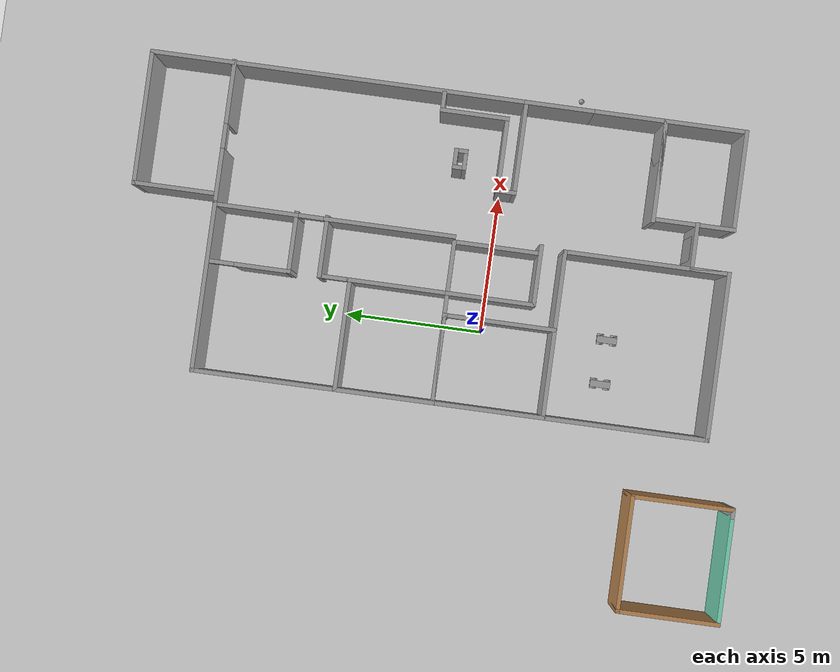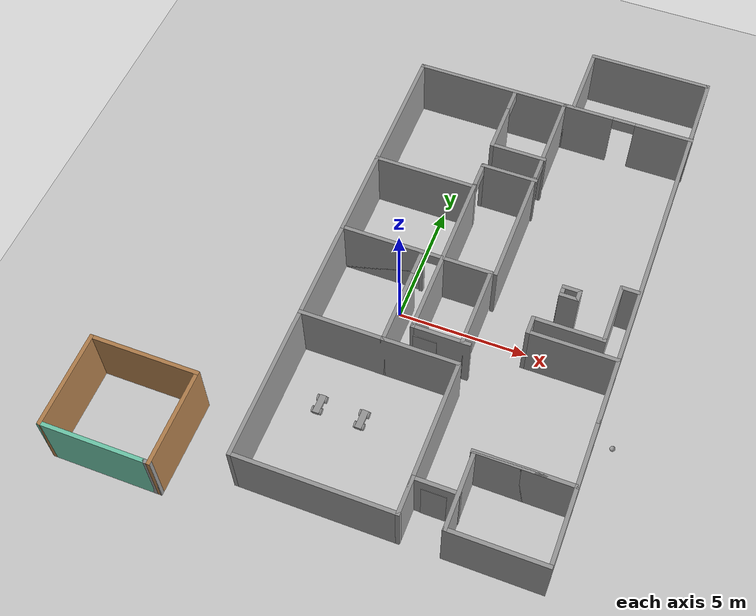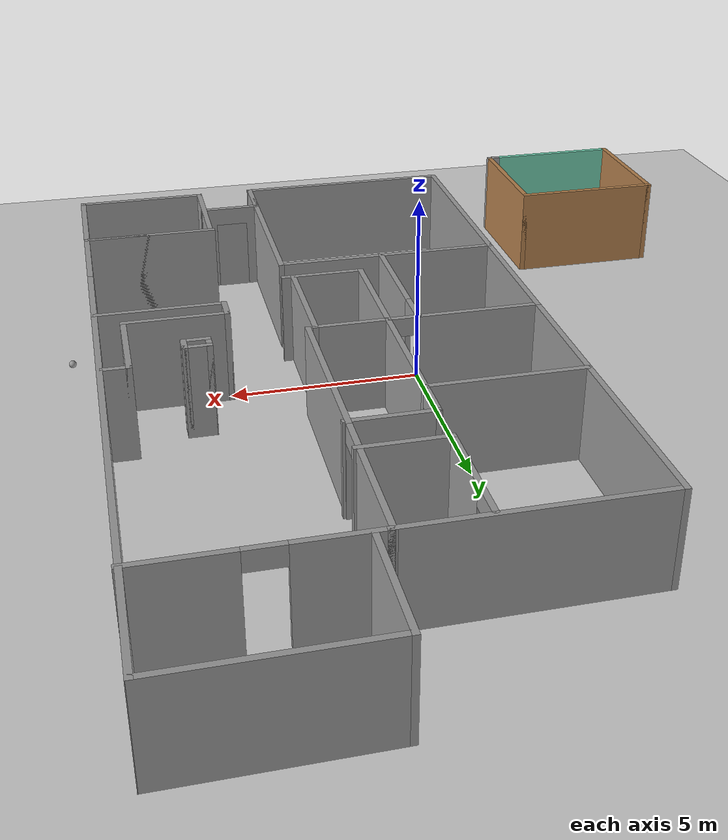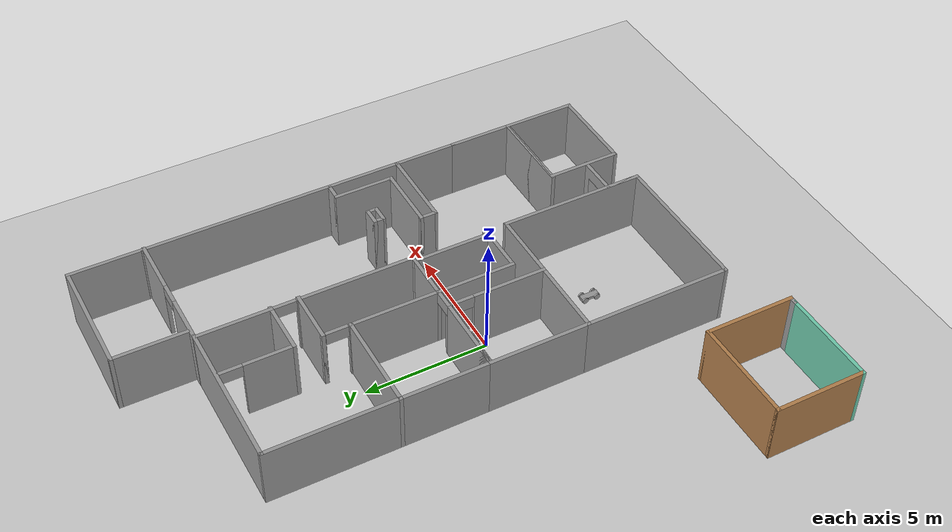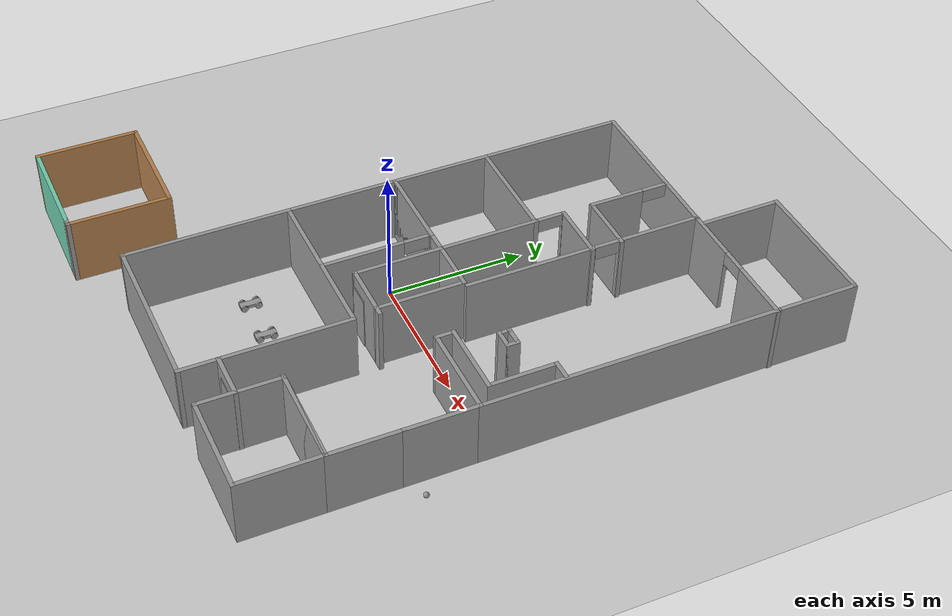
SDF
<sdf version="1.6">
 <world name="default">
  <plugin name="hello" filename="libhello.so"/>
  <light name="sun" type="directional">
   <pose>0 0 10 0 -0 0</pose>
   <diffuse>0.8 0.8 0.8 1</diffuse>
   <specular>0.2 0.2 0.2 1</specular>
   <attenuation>
    <range>1000</range>
    <constant>0.9</constant>
    <linear>0.01</linear>
    <quadratic>0.001</quadratic>
   </attenuation>
   <direction>-0.5 0.1 -0.9</direction>
  </light>
  <model name="ground_plane">
   <static>1</static>
   <link name="link">
    <collision name="collision">
     <geometry><plane><normal>0 0 1</normal><size>100 100</size></plane></geometry>
     <surface>
      <contact><collide_bitmask>65535</collide_bitmask></contact>
      <friction><ode><mu>100</mu><mu2>50</mu2></ode></friction>
     </surface>
    </collision>
    <visual name="visual">
     <cast_shadows>0</cast_shadows>
     <geometry><plane><normal>0 0 1</normal><size>100 100</size></plane></geometry>
     <material>
      <script><uri>file://media/materials/scripts/gazebo.material</uri><name>Gazebo/Grey</name></script>
     </material>
    </visual>
   </link>
  </model>
  <gravity>0 0 -9.8</gravity>
  <magnetic_field>6e-06 2.3e-05 -4.2e-05</magnetic_field>
  <atmosphere type="adiabatic"/>
  <physics name="default_physics" default="0" type="ode">
   <max_step_size>0.001</max_step_size>
   <real_time_factor>1</real_time_factor>
   <real_time_update_rate>1000</real_time_update_rate>
  </physics>
  <scene><ambient>0.4 0.4 0.4 1</ambient><background>0.7 0.7 0.7 1</background><shadows>1</shadows></scene>
  <spherical_coordinates>
   <surface_model>EARTH_WGS84</surface_model>
   <latitude_deg>0</latitude_deg>
   <longitude_deg>0</longitude_deg>
   <elevation>0</elevation>
   <heading_deg>0</heading_deg>
  </spherical_coordinates>
  <model name="WoodBlue">
   <pose>-7.16867 -7.90028 0 0 -0 0</pose>
   <link name="Wall_0">
    <collision name="Wall_0_Collision">
     <geometry><box><size>4 0.15 2.5</size></box></geometry>
     <pose>0 0 1.25 0 -0 0</pose>
    </collision>
    <visual name="Wall_0_Visual">
     <pose>0 0 1.25 0 -0 0</pose>
     <geometry><box><size>4 0.15 2.5</size></box></geometry>
     <material>
      <script><uri>file://media/materials/scripts/gazebo.material</uri><name>Gazebo/Grey</name></script>
      <ambient>0.435294 0.796078 0.67451 1</ambient>
     </material>
     <meta><layer>0</layer></meta>
    </visual>
    <pose>-0.125 -1.8 0 0 -0 0</pose>
   </link>
   <link name="Wall_3">
    <collision name="Wall_3_Collision">
     <geometry><box><size>3.75 0.15 2.5</size></box></geometry>
     <pose>0 0 1.25 0 -0 0</pose>
    </collision>
    <visual name="Wall_3_Visual">
     <pose>0 0 1.25 0 -0 0</pose>
     <geometry><box><size>3.75 0.15 2.5</size></box></geometry>
     <material>
      <script><uri>file://media/materials/scripts/gazebo.material</uri><name>Gazebo/Wood</name></script>
      <ambient>1 1 1 1</ambient>
     </material>
     <meta><layer>0</layer></meta>
    </visual>
    <pose>-2.05 0 0 0 -0 1.5708</pose>
   </link>
   <link name="Wall_4">
    <collision name="Wall_4_Collision">
     <geometry><box><size>4.25 0.15 2.5</size></box></geometry>
     <pose>0 0 1.25 0 -0 0</pose>
    </collision>
    <visual name="Wall_4_Visual">
     <pose>0 0 1.25 0 -0 0</pose>
     <geometry><box><size>4.25 0.15 2.5</size></box></geometry>
     <material>
      <script><uri>file://media/materials/scripts/gazebo.material</uri><name>Gazebo/Wood</name></script>
      <ambient>1 1 1 1</ambient>
     </material>
     <meta><layer>0</layer></meta>
    </visual>
    <pose>0 1.8 0 0 -0 0</pose>
   </link>
   <link name="Wall_5">
    <collision name="Wall_5_Collision">
     <geometry><box><size>3.75 0.15 2.5</size></box></geometry>
     <pose>0 0 1.25 0 -0 0</pose>
    </collision>
    <visual name="Wall_5_Visual">
     <pose>0 0 1.25 0 -0 0</pose>
     <geometry><box><size>3.75 0.15 2.5</size></box></geometry>
     <material>
      <script><uri>file://media/materials/scripts/gazebo.material</uri><name>Gazebo/Wood</name></script>
      <ambient>1 1 1 1</ambient>
     </material>
     <meta><layer>0</layer></meta>
    </visual>
    <pose>2.05 0 0 0 0 -1.5708</pose>
   </link>
   <link name="Wall_6">
    <collision name="Wall_6_Collision">
     <geometry><box><size>0.4 0.15 2.5</size></box></geometry>
     <pose>0 0 1.25 0 -0 0</pose>
    </collision>
    <visual name="Wall_6_Visual">
     <pose>0 0 1.25 0 -0 0</pose>
     <geometry><box><size>0.4 0.15 2.5</size></box></geometry>
     <material>
      <script><uri>file://media/materials/scripts/gazebo.material</uri><name>Gazebo/Grey</name></script>
      <ambient>1 1 1 1</ambient>
     </material>
     <meta><layer>0</layer></meta>
    </visual>
    <pose>1.925 -1.8 0 0 0 -3.14159</pose>
   </link>
   <static>1</static>
  </model>
  <model name="Model_House">
   <pose>2.76845 2.28145 0 0 -0 0</pose>
   <link name="Door_0">
    <collision name="Door_0_Collision">
     <geometry><box><size>0.9 0.17 2</size></box></geometry>
     <pose>0 0 1 0 -0 0</pose>
    </collision>
    <visual name="Door_0_Visual">
     <pose>0 0 1 0 -0 0</pose>
     <geometry><box><size>0.9 0.17 2</size></box></geometry>
     <material>
      <script><uri>file://media/materials/scripts/gazebo.material</uri><name>Gazebo/Grey</name></script>
     </material>
    </visual>
    <pose>1.18113 -9.39203 0 0 -0 0</pose>
   </link>
   <link name="Door_5">
    <collision name="Door_5_Collision">
     <geometry><box><size>0.9 0.17 2</size></box></geometry>
     <pose>0 0 1 0 -0 0</pose>
    </collision>
    <visual name="Door_5_Visual">
     <pose>0 0 1 0 -0 0</pose>
     <geometry><box><size>0.9 0.17 2</size></box></geometry>
     <material>
      <script><uri>file://media/materials/scripts/gazebo.material</uri><name>Gazebo/Grey</name></script>
     </material>
    </visual>
    <pose>-1.13265 -3.99754 0 0 -0 0</pose>
   </link>
   <link name="Wall_0">
    <collision name="Wall_0_Collision">
     <geometry><box><size>3.683 0.15 2.5</size></box></geometry>
     <pose>0 0 1.25 0 -0 0</pose>
    </collision>
    <visual name="Wall_0_Visual">
     <pose>0 0 1.25 0 -0 0</pose>
     <geometry><box><size>3.683 0.15 2.5</size></box></geometry>
     <material>
      <script><uri>file://media/materials/scripts/gazebo.material</uri><name>Gazebo/Grey</name></script>
      <ambient>1 1 1 1</ambient>
     </material>
     <meta><layer>0</layer></meta>
    </visual>
    <pose>3.75781 -10.694 0 0 -0 0</pose>
   </link>
   <link name="Wall_103">
    <collision name="Wall_103_Collision">
     <geometry><box><size>10.75 0.15 2.5</size></box></geometry>
     <pose>0 0 1.25 0 -0 0</pose>
    </collision>
    <visual name="Wall_103_Visual">
     <pose>0 0 1.25 0 -0 0</pose>
     <geometry><box><size>10.75 0.15 2.5</size></box></geometry>
     <material>
      <script><uri>file://media/materials/scripts/gazebo.material</uri><name>Gazebo/Grey</name></script>
      <ambient>1 1 1 1</ambient>
     </material>
     <meta><layer>0</layer></meta>
    </visual>
    <pose>5.52431 2.53801 0 0 -0 1.5708</pose>
   </link>
   <link name="Wall_115">
    <collision name="Wall_115_Collision">
     <geometry><box><size>0.75 0.15 2.5</size></box></geometry>
     <pose>0 0 1.25 0 -0 0</pose>
    </collision>
    <visual name="Wall_115_Visual">
     <pose>0 0 1.25 0 -0 0</pose>
     <geometry><box><size>0.75 0.15 2.5</size></box></geometry>
     <material>
      <script><uri>file://media/materials/scripts/gazebo.material</uri><name>Gazebo/Grey</name></script>
      <ambient>1 1 1 1</ambient>
     </material>
     <meta><layer>0</layer></meta>
    </visual>
    <pose>2.24531 -2.46199 0 0 -0 1.5708</pose>
   </link>
   <link name="Wall_116">
    <collision name="Wall_116_Collision">
     <geometry><box><size>2.75 0.15 2.5</size></box></geometry>
     <pose>0 0 1.25 0 -0 0</pose>
    </collision>
    <visual name="Wall_116_Visual">
     <pose>0 0 1.25 0 -0 0</pose>
     <geometry><box><size>2.75 0.15 2.5</size></box></geometry>
     <material>
      <script><uri>file://media/materials/scripts/gazebo.material</uri><name>Gazebo/Grey</name></script>
      <ambient>1 1 1 1</ambient>
     </material>
     <meta><layer>0</layer></meta>
    </visual>
    <pose>3.54531 -2.16199 0 0 -0 0</pose>
   </link>
   <link name="Wall_117">
    <collision name="Wall_117_Collision">
     <geometry><box><size>2.5 0.15 2.5</size></box></geometry>
     <pose>0 0 1.25 0 -0 0</pose>
    </collision>
    <visual name="Wall_117_Visual">
     <pose>0 0 1.25 0 -0 0</pose>
     <geometry><box><size>2.5 0.15 2.5</size></box></geometry>
     <material>
      <script><uri>file://media/materials/scripts/gazebo.material</uri><name>Gazebo/Grey</name></script>
      <ambient>1 1 1 1</ambient>
     </material>
     <meta><layer>0</layer></meta>
    </visual>
    <pose>4.84531 -0.986987 0 0 -0 1.5708</pose>
   </link>
   <link name="Wall_118">
    <collision name="Wall_118_Collision">
     <geometry><box><size>0.75 0.15 2.5</size></box></geometry>
     <pose>0 0 1.25 0 -0 0</pose>
    </collision>
    <visual name="Wall_118_Visual">
     <pose>0 0 1.25 0 -0 0</pose>
     <geometry><box><size>0.75 0.15 2.5</size></box></geometry>
     <material>
      <script><uri>file://media/materials/scripts/gazebo.material</uri><name>Gazebo/Grey</name></script>
      <ambient>1 1 1 1</ambient>
     </material>
     <meta><layer>0</layer></meta>
    </visual>
    <pose>5.14531 0.188013 0 0 -0 0</pose>
   </link>
   <link name="Wall_12">
    <collision name="Wall_12_Collision">
     <geometry><box><size>3.048 0.15 2.5</size></box></geometry>
     <pose>0 0 1.25 0 -0 0</pose>
    </collision>
    <visual name="Wall_12_Visual">
     <pose>0 0 1.25 0 -0 0</pose>
     <geometry><box><size>3.048 0.15 2.5</size></box></geometry>
     <material>
      <script><uri>file://media/materials/scripts/gazebo.material</uri><name>Gazebo/Grey</name></script>
      <ambient>1 1 1 1</ambient>
     </material>
     <meta><layer>0</layer></meta>
    </visual>
    <pose>5.52431 -9.24499 0 0 -0 1.5708</pose>
   </link>
   <link name="Wall_120">
    <collision name="Wall_120_Collision">
     <geometry><box><size>0.75 0.15 2.5</size></box></geometry>
     <pose>0 0 1.25 0 -0 0</pose>
    </collision>
    <visual name="Wall_120_Visual">
     <pose>0 0 1.25 0 -0 0</pose>
     <geometry><box><size>0.75 0.15 2.5</size></box></geometry>
     <material>
      <script><uri>file://media/materials/scripts/gazebo.material</uri><name>Gazebo/Grey</name></script>
      <ambient>1 1 1 1</ambient>
     </material>
     <meta><layer>0</layer></meta>
    </visual>
    <pose>3.18422 -0.509456 0 0 -0 0</pose>
   </link>
   <link name="Wall_121">
    <collision name="Wall_121_Collision">
     <geometry><box><size>0.5 0.15 2.5</size></box></geometry>
     <pose>0 0 1.25 0 -0 0</pose>
    </collision>
    <visual name="Wall_121_Visual">
     <pose>0 0 1.25 0 -0 0</pose>
     <geometry><box><size>0.5 0.15 2.5</size></box></geometry>
     <material>
      <script><uri>file://media/materials/scripts/gazebo.material</uri><name>Gazebo/Grey</name></script>
      <ambient>1 1 1 1</ambient>
     </material>
     <meta><layer>0</layer></meta>
    </visual>
    <pose>3.48422 -0.684456 0 0 0 -1.5708</pose>
   </link>
   <link name="Wall_122">
    <collision name="Wall_122_Collision">
     <geometry><box><size>0.75 0.15 2.5</size></box></geometry>
     <pose>0 0 1.25 0 -0 0</pose>
    </collision>
    <visual name="Wall_122_Visual">
     <pose>0 0 1.25 0 -0 0</pose>
     <geometry><box><size>0.75 0.15 2.5</size></box></geometry>
     <material>
      <script><uri>file://media/materials/scripts/gazebo.material</uri><name>Gazebo/Grey</name></script>
      <ambient>1 1 1 1</ambient>
     </material>
     <meta><layer>0</layer></meta>
    </visual>
    <pose>3.18422 -0.859456 0 0 -0 3.14159</pose>
   </link>
   <link name="Wall_123">
    <collision name="Wall_123_Collision">
     <geometry><box><size>0.5 0.15 2.5</size></box></geometry>
     <pose>0 0 1.25 0 -0 0</pose>
    </collision>
    <visual name="Wall_123_Visual">
     <pose>0 0 1.25 0 -0 0</pose>
     <geometry><box><size>0.5 0.15 2.5</size></box></geometry>
     <material>
      <script><uri>file://media/materials/scripts/gazebo.material</uri><name>Gazebo/Grey</name></script>
      <ambient>1 1 1 1</ambient>
     </material>
     <meta><layer>0</layer></meta>
    </visual>
    <pose>2.88422 -0.684456 0 0 -0 1.5708</pose>
   </link>
   <link name="Wall_126">
    <collision name="Wall_126_Collision">
     <geometry><box><size>4.877 0.15 2.5</size></box></geometry>
     <pose>0 0 1.25 0 -0 0</pose>
    </collision>
    <visual name="Wall_126_Visual">
     <pose>0 0 1.25 0 -0 0</pose>
     <geometry><box><size>4.877 0.15 2.5</size></box></geometry>
     <material>
      <script><uri>file://media/materials/scripts/gazebo.material</uri><name>Gazebo/Grey</name></script>
      <ambient>1 1 1 1</ambient>
     </material>
     <meta><layer>0</layer></meta>
    </visual>
    <pose>3.14687 10.7361 0 0 -0 0</pose>
   </link>
   <link name="Wall_128">
    <collision name="Wall_128_Collision">
     <geometry><box><size>3.048 0.15 2.5</size></box></geometry>
     <pose>0 0 1.25 0 -0 0</pose>
    </collision>
    <visual name="Wall_128_Visual">
     <pose>0 0 1.25 0 -0 0</pose>
     <geometry><box><size>3.048 0.15 2.5</size></box></geometry>
     <material>
      <script><uri>file://media/materials/scripts/gazebo.material</uri><name>Gazebo/Grey</name></script>
      <ambient>1 1 1 1</ambient>
     </material>
     <meta><layer>0</layer></meta>
    </visual>
    <pose>5.52431 9.28701 0 0 -0 1.5708</pose>
   </link>
   <link name="Wall_130">
    <collision name="Wall_130_Collision">
     <geometry><box><size>3 0.15 2.5</size></box></geometry>
     <pose>0 0 1.25 0 -0 0</pose>
    </collision>
    <visual name="Wall_130_Visual">
     <pose>0 0 1.25 0 -0 0</pose>
     <geometry><box><size>3 0.15 2.5</size></box></geometry>
     <material>
      <script><uri>file://media/materials/scripts/gazebo.material</uri><name>Gazebo/Grey</name></script>
      <ambient>1 1 1 1</ambient>
     </material>
     <meta><layer>0</layer></meta>
    </visual>
    <pose>0.783373 9.31114 0 0 0 -1.5708</pose>
   </link>
   <link name="Wall_14">
    <collision name="Wall_14_Collision">
     <geometry><box><size>3.048 0.15 2.5</size></box></geometry>
     <pose>0 0 1.25 0 -0 0</pose>
    </collision>
    <visual name="Wall_14_Visual">
     <pose>0 0 1.25 0 -0 0</pose>
     <geometry><box><size>3.048 0.15 2.5</size></box></geometry>
     <material>
      <script><uri>file://media/materials/scripts/gazebo.material</uri><name>Gazebo/Grey</name></script>
      <ambient>1 1 1 1</ambient>
     </material>
     <meta><layer>0</layer></meta>
    </visual>
    <pose>1.99131 -9.24499 0 0 -0 1.5708</pose>
   </link>
   <link name="Wall_16">
    <collision name="Wall_16_Collision">
     <geometry><box><size>3.683 0.15 2.5</size></box></geometry>
     <pose>0 0 1.25 0 -0 0</pose>
    </collision>
    <visual name="Wall_16_Visual">
     <pose>0 0 1.25 0 -0 0</pose>
     <geometry><box><size>3.683 0.15 2.5</size></box></geometry>
     <material>
      <script><uri>file://media/materials/scripts/gazebo.material</uri><name>Gazebo/Grey</name></script>
      <ambient>1 1 1 1</ambient>
     </material>
     <meta><layer>0</layer></meta>
    </visual>
    <pose>3.75781 -7.79599 0 0 -0 0</pose>
   </link>
   <link name="Wall_18">
    <collision name="Wall_18_Collision">
     <geometry><box><size>2.667 0.15 2.5</size></box></geometry>
     <pose>0 0 1.25 0 -0 0</pose>
    </collision>
    <visual name="Wall_18_Visual">
     <pose>0 0 1.25 0 -0 0</pose>
     <geometry><box><size>2.667 0.15 2.5</size></box></geometry>
     <material>
      <script><uri>file://media/materials/scripts/gazebo.material</uri><name>Gazebo/Grey</name></script>
      <ambient>1 1 1 1</ambient>
     </material>
     <meta><layer>0</layer></meta>
    </visual>
    <pose>5.52431 -6.53749 0 0 -0 1.5708</pose>
   </link>
   <link name="Wall_20">
    <collision name="Wall_20_Collision">
     <geometry><box><size>3.733 0.15 2.5</size></box></geometry>
     <pose>0 0 1.25 0 -0 0</pose>
    </collision>
    <visual name="Wall_20_Visual">
     <pose>0 0 1.25 0 -0 0</pose>
     <geometry><box><size>3.733 0.15 2.5</size></box></geometry>
     <material>
      <script><uri>file://media/materials/scripts/gazebo.material</uri><name>Gazebo/Grey</name></script>
      <ambient>1 1 1 1</ambient>
     </material>
     <meta><layer>0</layer></meta>
    </visual>
    <pose>3.73281 -7.79599 0 0 -0 3.14159</pose>
   </link>
   <link name="Wall_22">
    <collision name="Wall_22_Collision">
     <geometry><box><size>2.667 0.15 2.5</size></box></geometry>
     <pose>0 0 1.25 0 -0 0</pose>
    </collision>
    <visual name="Wall_22_Visual">
     <pose>0 0 1.25 0 -0 0</pose>
     <geometry><box><size>2.667 0.15 2.5</size></box></geometry>
     <material>
      <script><uri>file://media/materials/scripts/gazebo.material</uri><name>Gazebo/Grey</name></script>
      <ambient>1 1 1 1</ambient>
     </material>
     <meta><layer>0</layer></meta>
    </visual>
    <pose>5.52431 -4.02049 0 0 -0 1.5708</pose>
   </link>
   <link name="Wall_24">
    <collision name="Wall_24_Collision">
     <geometry><box><size>3.429 0.15 2.5</size></box></geometry>
     <pose>0 0 1.25 0 -0 0</pose>
    </collision>
    <visual name="Wall_24_Visual">
     <pose>0 0 1.25 0 -0 0</pose>
     <geometry><box><size>3.429 0.15 2.5</size></box></geometry>
     <material>
      <script><uri>file://media/materials/scripts/gazebo.material</uri><name>Gazebo/Grey</name></script>
      <ambient>1 1 1 1</ambient>
     </material>
     <meta><layer>0</layer></meta>
    </visual>
    <pose>3.88481 -2.76199 0 0 -0 3.14159</pose>
   </link>
   <link name="Wall_26">
    <collision name="Wall_26_Collision">
     <geometry><box><size>1.75 0.15 2.5</size></box></geometry>
     <pose>0 0 1.25 0 -0 0</pose>
    </collision>
    <visual name="Wall_26_Visual">
     <pose>0 0 1.25 0 -0 0</pose>
     <geometry><box><size>1.75 0.15 2.5</size></box></geometry>
     <material>
      <script><uri>file://media/materials/scripts/gazebo.material</uri><name>Gazebo/Grey</name></script>
      <ambient>1 1 1 1</ambient>
     </material>
     <meta><layer>0</layer></meta>
    </visual>
    <pose>1.20969 -9.38615 0 0 -0 3.14159</pose>
   </link>
   <link name="Wall_28">
    <collision name="Wall_28_Collision">
     <geometry><box><size>1.5 0.15 2.5</size></box></geometry>
     <pose>0 0 1.25 0 -0 0</pose>
    </collision>
    <visual name="Wall_28_Visual">
     <pose>0 0 1.25 0 -0 0</pose>
     <geometry><box><size>1.5 0.15 2.5</size></box></geometry>
     <material>
      <script><uri>file://media/materials/scripts/gazebo.material</uri><name>Gazebo/Grey</name></script>
      <ambient>1 1 1 1</ambient>
     </material>
     <meta><layer>0</layer></meta>
    </visual>
    <pose>0.409687 -10.0611 0 0 0 -1.5708</pose>
   </link>
   <link name="Wall_30">
    <collision name="Wall_30_Collision">
     <geometry><box><size>6.121 0.15 2.5</size></box></geometry>
     <pose>0 0 1.25 0 -0 0</pose>
    </collision>
    <visual name="Wall_30_Visual">
     <pose>0 0 1.25 0 -0 0</pose>
     <geometry><box><size>6.121 0.15 2.5</size></box></geometry>
     <material>
      <script><uri>file://media/materials/scripts/gazebo.material</uri><name>Gazebo/Grey</name></script>
      <ambient>1 1 1 1</ambient>
     </material>
     <meta><layer>0</layer></meta>
    </visual>
    <pose>-2.57581 -10.7361 0 0 -0 3.14159</pose>
   </link>
   <link name="Wall_32">
    <collision name="Wall_32_Collision">
     <geometry><box><size>6.045 0.15 2.5</size></box></geometry>
     <pose>0 0 1.25 0 -0 0</pose>
    </collision>
    <visual name="Wall_32_Visual">
     <pose>0 0 1.25 0 -0 0</pose>
     <geometry><box><size>6.045 0.15 2.5</size></box></geometry>
     <material>
      <script><uri>file://media/materials/scripts/gazebo.material</uri><name>Gazebo/Grey</name></script>
      <ambient>1 1 1 1</ambient>
     </material>
     <meta><layer>0</layer></meta>
    </visual>
    <pose>-5.56131 -7.78864 0 0 -0 1.5708</pose>
   </link>
   <link name="Wall_34">
    <collision name="Wall_34_Collision">
     <geometry><box><size>6.121 0.15 2.5</size></box></geometry>
     <pose>0 0 1.25 0 -0 0</pose>
    </collision>
    <visual name="Wall_34_Visual">
     <pose>0 0 1.25 0 -0 0</pose>
     <geometry><box><size>6.121 0.15 2.5</size></box></geometry>
     <material>
      <script><uri>file://media/materials/scripts/gazebo.material</uri><name>Gazebo/Grey</name></script>
      <ambient>1 1 1 1</ambient>
     </material>
     <meta><layer>0</layer></meta>
    </visual>
    <pose>-2.57581 -4.84115 0 0 -0 0</pose>
   </link>
   <link name="Wall_36">
    <collision name="Wall_36_Collision">
     <geometry><box><size>6.045 0.15 2.5</size></box></geometry>
     <pose>0 0 1.25 0 -0 0</pose>
    </collision>
    <visual name="Wall_36_Visual">
     <pose>0 0 1.25 0 -0 0</pose>
     <geometry><box><size>6.045 0.15 2.5</size></box></geometry>
     <material>
      <script><uri>file://media/materials/scripts/gazebo.material</uri><name>Gazebo/Grey</name></script>
      <ambient>1 1 1 1</ambient>
     </material>
     <meta><layer>0</layer></meta>
    </visual>
    <pose>0.409687 -7.78864 0 0 0 -1.5708</pose>
   </link>
   <link name="Wall_38">
    <collision name="Wall_38_Collision">
     <geometry><box><size>4.115 0.15 2.5</size></box></geometry>
     <pose>0 0 1.25 0 -0 0</pose>
    </collision>
    <visual name="Wall_38_Visual">
     <pose>0 0 1.25 0 -0 0</pose>
     <geometry><box><size>4.115 0.15 2.5</size></box></geometry>
     <material>
      <script><uri>file://media/materials/scripts/gazebo.material</uri><name>Gazebo/Grey</name></script>
      <ambient>1 1 1 1</ambient>
     </material>
     <meta><layer>0</layer></meta>
    </visual>
    <pose>-5.56131 -2.85865 0 0 -0 1.5708</pose>
   </link>
   <link name="Wall_40">
    <collision name="Wall_40_Collision">
     <geometry><box><size>3.302 0.15 2.5</size></box></geometry>
     <pose>0 0 1.25 0 -0 0</pose>
    </collision>
    <visual name="Wall_40_Visual">
     <pose>0 0 1.25 0 -0 0</pose>
     <geometry><box><size>3.302 0.15 2.5</size></box></geometry>
     <material>
      <script><uri>file://media/materials/scripts/gazebo.material</uri><name>Gazebo/Grey</name></script>
      <ambient>1 1 1 1</ambient>
     </material>
     <meta><layer>0</layer></meta>
    </visual>
    <pose>-3.98531 -0.876145 0 0 -0 0</pose>
   </link>
   <link name="Wall_42">
    <pose>-2.40931 -2.85865 0 0 0 -1.5708</pose>
    <visual name="Wall_42_Visual_0">
     <pose>-1.95969 0 1.25 0 -0 0</pose>
     <geometry><box><size>0.195618 0.15 2.5</size></box></geometry>
     <material>
      <script><uri>file://media/materials/scripts/gazebo.material</uri><name>Gazebo/Grey</name></script>
      <ambient>1 1 1 1</ambient>
     </material>
     <meta><layer>0</layer></meta>
    </visual>
    <collision name="Wall_42_Collision_0">
     <geometry><box><size>0.195618 0.15 2.5</size></box></geometry>
     <pose>-1.95969 0 1.25 0 -0 0</pose>
    </collision>
    <visual name="Wall_42_Visual_1">
     <pose>0.547809 0 1.25 0 -0 0</pose>
     <geometry><box><size>3.01938 0.15 2.5</size></box></geometry>
     <material>
      <script><uri>file://media/materials/scripts/gazebo.material</uri><name>Gazebo/Grey</name></script>
      <ambient>1 1 1 1</ambient>
     </material>
     <meta><layer>0</layer></meta>
    </visual>
    <collision name="Wall_42_Collision_1">
     <geometry><box><size>3.01938 0.15 2.5</size></box></geometry>
     <pose>0.547809 0 1.25 0 -0 0</pose>
    </collision>
    <visual name="Wall_42_Visual_2">
     <pose>-1.41188 0 2.25 0 -0 0</pose>
     <geometry><box><size>0.9 0.15 0.5</size></box></geometry>
     <material>
      <script><uri>file://media/materials/scripts/gazebo.material</uri><name>Gazebo/Grey</name></script>
      <ambient>1 1 1 1</ambient>
     </material>
     <meta><layer>0</layer></meta>
    </visual>
    <collision name="Wall_42_Collision_2">
     <geometry><box><size>0.9 0.15 0.5</size></box></geometry>
     <pose>-1.41188 0 2.25 0 -0 0</pose>
    </collision>
   </link>
   <link name="Wall_44">
    <pose>-3.59181 -0.876145 0 0 -0 0</pose>
    <visual name="Wall_44_Visual_0">
     <pose>-0.45674 0 1.25 0 -0 0</pose>
     <geometry><box><size>3.17552 0.15 2.5</size></box></geometry>
     <material>
      <script><uri>file://media/materials/scripts/gazebo.material</uri><name>Gazebo/Grey</name></script>
      <ambient>1 1 1 1</ambient>
     </material>
     <meta><layer>0</layer></meta>
    </visual>
    <collision name="Wall_44_Collision_0">
     <geometry><box><size>3.17552 0.15 2.5</size></box></geometry>
     <pose>-0.45674 0 1.25 0 -0 0</pose>
    </collision>
    <visual name="Wall_44_Visual_1">
     <pose>2.03776 0 1.25 0 -0 0</pose>
     <geometry><box><size>0.013479 0.15 2.5</size></box></geometry>
     <material>
      <script><uri>file://media/materials/scripts/gazebo.material</uri><name>Gazebo/Grey</name></script>
      <ambient>1 1 1 1</ambient>
     </material>
     <meta><layer>0</layer></meta>
    </visual>
    <collision name="Wall_44_Collision_1">
     <geometry><box><size>0.013479 0.15 2.5</size></box></geometry>
     <pose>2.03776 0 1.25 0 -0 0</pose>
    </collision>
    <visual name="Wall_44_Visual_2">
     <pose>1.58102 0 2.25 0 -0 0</pose>
     <geometry><box><size>0.9 0.15 0.5</size></box></geometry>
     <material>
      <script><uri>file://media/materials/scripts/gazebo.material</uri><name>Gazebo/Grey</name></script>
      <ambient>1 1 1 1</ambient>
     </material>
     <meta><layer>0</layer></meta>
    </visual>
    <collision name="Wall_44_Collision_2">
     <geometry><box><size>0.9 0.15 0.5</size></box></geometry>
     <pose>1.58102 0 2.25 0 -0 0</pose>
    </collision>
   </link>
   <link name="Wall_48">
    <collision name="Wall_48_Collision">
     <geometry><box><size>3.658 0.15 2.5</size></box></geometry>
     <pose>0 0 1.25 0 -0 0</pose>
    </collision>
    <visual name="Wall_48_Visual">
     <pose>0 0 1.25 0 -0 0</pose>
     <geometry><box><size>3.658 0.15 2.5</size></box></geometry>
     <material>
      <script><uri>file://media/materials/scripts/gazebo.material</uri><name>Gazebo/Grey</name></script>
      <ambient>1 1 1 1</ambient>
     </material>
     <meta><layer>0</layer></meta>
    </visual>
    <pose>-1.62231 0.877855 0 0 -0 1.5708</pose>
   </link>
   <link name="Wall_50">
    <collision name="Wall_50_Collision">
     <geometry><box><size>4.089 0.15 2.5</size></box></geometry>
     <pose>0 0 1.25 0 -0 0</pose>
    </collision>
    <visual name="Wall_50_Visual">
     <pose>0 0 1.25 0 -0 0</pose>
     <geometry><box><size>4.089 0.15 2.5</size></box></geometry>
     <material>
      <script><uri>file://media/materials/scripts/gazebo.material</uri><name>Gazebo/Grey</name></script>
      <ambient>1 1 1 1</ambient>
     </material>
     <meta><layer>0</layer></meta>
    </visual>
    <pose>-3.59181 2.63185 0 0 -0 3.14159</pose>
   </link>
   <link name="Wall_52">
    <collision name="Wall_52_Collision">
     <geometry><box><size>3.658 0.15 2.5</size></box></geometry>
     <pose>0 0 1.25 0 -0 0</pose>
    </collision>
    <visual name="Wall_52_Visual">
     <pose>0 0 1.25 0 -0 0</pose>
     <geometry><box><size>3.658 0.15 2.5</size></box></geometry>
     <material>
      <script><uri>file://media/materials/scripts/gazebo.material</uri><name>Gazebo/Grey</name></script>
      <ambient>1 1 1 1</ambient>
     </material>
     <meta><layer>0</layer></meta>
    </visual>
    <pose>-5.56131 0.877855 0 0 0 -1.5708</pose>
   </link>
   <link name="Wall_54">
    <collision name="Wall_54_Collision">
     <geometry><box><size>5.283 0.15 2.5</size></box></geometry>
     <pose>0 0 1.25 0 -0 0</pose>
    </collision>
    <visual name="Wall_54_Visual">
     <pose>0 0 1.25 0 -0 0</pose>
     <geometry><box><size>5.283 0.15 2.5</size></box></geometry>
     <material>
      <script><uri>file://media/materials/scripts/gazebo.material</uri><name>Gazebo/Grey</name></script>
      <ambient>1 1 1 1</ambient>
     </material>
     <meta><layer>0</layer></meta>
    </visual>
    <pose>-5.56131 5.19836 0 0 -0 1.5708</pose>
   </link>
   <link name="Wall_56">
    <collision name="Wall_56_Collision">
     <geometry><box><size>6.125 0.15 2.5</size></box></geometry>
     <pose>0 0 1.25 0 -0 0</pose>
    </collision>
    <visual name="Wall_56_Visual">
     <pose>0 0 1.25 0 -0 0</pose>
     <geometry><box><size>6.125 0.15 2.5</size></box></geometry>
     <material>
      <script><uri>file://media/materials/scripts/gazebo.material</uri><name>Gazebo/Grey</name></script>
      <ambient>1 1 1 1</ambient>
     </material>
     <meta><layer>0</layer></meta>
    </visual>
    <pose>-2.57381 7.76485 0 0 -0 0</pose>
   </link>
   <link name="Wall_62">
    <pose>-1.62231 3.18186 0 0 -0 1.5708</pose>
    <visual name="Wall_62_Visual_0">
     <pose>-0.531106 0 1.25 0 -0 0</pose>
     <geometry><box><size>0.187788 0.15 2.5</size></box></geometry>
     <material>
      <script><uri>file://media/materials/scripts/gazebo.material</uri><name>Gazebo/Grey</name></script>
      <ambient>1 1 1 1</ambient>
     </material>
     <meta><layer>0</layer></meta>
    </visual>
    <collision name="Wall_62_Collision_0">
     <geometry><box><size>0.187788 0.15 2.5</size></box></geometry>
     <pose>-0.531106 0 1.25 0 -0 0</pose>
    </collision>
    <visual name="Wall_62_Visual_1">
     <pose>0.543894 0 1.25 0 -0 0</pose>
     <geometry><box><size>0.162212 0.15 2.5</size></box></geometry>
     <material>
      <script><uri>file://media/materials/scripts/gazebo.material</uri><name>Gazebo/Grey</name></script>
      <ambient>1 1 1 1</ambient>
     </material>
     <meta><layer>0</layer></meta>
    </visual>
    <collision name="Wall_62_Collision_1">
     <geometry><box><size>0.162212 0.15 2.5</size></box></geometry>
     <pose>0.543894 0 1.25 0 -0 0</pose>
    </collision>
    <visual name="Wall_62_Visual_2">
     <pose>0.012788 0 2.25 0 -0 0</pose>
     <geometry><box><size>0.9 0.15 0.5</size></box></geometry>
     <material>
      <script><uri>file://media/materials/scripts/gazebo.material</uri><name>Gazebo/Grey</name></script>
      <ambient>1 1 1 1</ambient>
     </material>
     <meta><layer>0</layer></meta>
    </visual>
    <collision name="Wall_62_Collision_2">
     <geometry><box><size>0.9 0.15 0.5</size></box></geometry>
     <pose>0.012788 0 2.25 0 -0 0</pose>
    </collision>
   </link>
   <link name="Wall_64">
    <collision name="Wall_64_Collision">
     <geometry><box><size>2.25 0.15 2.5</size></box></geometry>
     <pose>0 0 1.25 0 -0 0</pose>
    </collision>
    <visual name="Wall_64_Visual">
     <pose>0 0 1.25 0 -0 0</pose>
     <geometry><box><size>2.25 0.15 2.5</size></box></geometry>
     <material>
      <script><uri>file://media/materials/scripts/gazebo.material</uri><name>Gazebo/Grey</name></script>
      <ambient>1 1 1 1</ambient>
     </material>
     <meta><layer>0</layer></meta>
    </visual>
    <pose>-0.572313 3.73185 0 0 -0 0</pose>
   </link>
   <link name="Wall_68">
    <collision name="Wall_68_Collision">
     <geometry><box><size>2.25 0.15 2.5</size></box></geometry>
     <pose>0 0 1.25 0 -0 0</pose>
    </collision>
    <visual name="Wall_68_Visual">
     <pose>0 0 1.25 0 -0 0</pose>
     <geometry><box><size>2.25 0.15 2.5</size></box></geometry>
     <material>
      <script><uri>file://media/materials/scripts/gazebo.material</uri><name>Gazebo/Grey</name></script>
      <ambient>1 1 1 1</ambient>
     </material>
     <meta><layer>0</layer></meta>
    </visual>
    <pose>-0.572313 4.83186 0 0 -0 0</pose>
   </link>
   <link name="Wall_70">
    <collision name="Wall_70_Collision">
     <geometry><box><size>3.25 0.15 2.5</size></box></geometry>
     <pose>0 0 1.25 0 -0 0</pose>
    </collision>
    <visual name="Wall_70_Visual">
     <pose>0 0 1.25 0 -0 0</pose>
     <geometry><box><size>3.25 0.15 2.5</size></box></geometry>
     <material>
      <script><uri>file://media/materials/scripts/gazebo.material</uri><name>Gazebo/Grey</name></script>
      <ambient>1 1 1 1</ambient>
     </material>
     <meta><layer>0</layer></meta>
    </visual>
    <pose>-1.62231 -2.42614 0 0 0 -1.5708</pose>
   </link>
   <link name="Wall_73">
    <collision name="Wall_73_Collision">
     <geometry><box><size>0.15 0.15 2.5</size></box></geometry>
     <pose>0 0 1.25 0 -0 0</pose>
    </collision>
    <visual name="Wall_73_Visual">
     <pose>0 0 1.25 0 -0 0</pose>
     <geometry><box><size>0.15 0.15 2.5</size></box></geometry>
     <material>
      <script><uri>file://media/materials/scripts/gazebo.material</uri><name>Gazebo/Grey</name></script>
      <ambient>1 1 1 1</ambient>
     </material>
     <meta><layer>0</layer></meta>
    </visual>
    <pose>0.461314 7.77224 0 0 -0 0</pose>
   </link>
   <link name="Wall_77">
    <pose>-1.62231 6.25685 0 0 -0 1.5708</pose>
    <visual name="Wall_77_Visual_0">
     <pose>-0.4829 0 1.25 0 -0 0</pose>
     <geometry><box><size>2.0342 0.15 2.5</size></box></geometry>
     <material>
      <script><uri>file://media/materials/scripts/gazebo.material</uri><name>Gazebo/Grey</name></script>
      <ambient>1 1 1 1</ambient>
     </material>
     <meta><layer>0</layer></meta>
    </visual>
    <collision name="Wall_77_Collision_0">
     <geometry><box><size>2.0342 0.15 2.5</size></box></geometry>
     <pose>-0.4829 0 1.25 0 -0 0</pose>
    </collision>
    <visual name="Wall_77_Visual_1">
     <pose>1.4671 0 1.25 0 -0 0</pose>
     <geometry><box><size>0.0658 0.15 2.5</size></box></geometry>
     <material>
      <script><uri>file://media/materials/scripts/gazebo.material</uri><name>Gazebo/Grey</name></script>
      <ambient>1 1 1 1</ambient>
     </material>
     <meta><layer>0</layer></meta>
    </visual>
    <collision name="Wall_77_Collision_1">
     <geometry><box><size>0.0658 0.15 2.5</size></box></geometry>
     <pose>1.4671 0 1.25 0 -0 0</pose>
    </collision>
    <visual name="Wall_77_Visual_2">
     <pose>0.9842 0 2.25 0 -0 0</pose>
     <geometry><box><size>0.9 0.15 0.5</size></box></geometry>
     <material>
      <script><uri>file://media/materials/scripts/gazebo.material</uri><name>Gazebo/Grey</name></script>
      <ambient>1 1 1 1</ambient>
     </material>
     <meta><layer>0</layer></meta>
    </visual>
    <collision name="Wall_77_Collision_2">
     <geometry><box><size>0.9 0.15 0.5</size></box></geometry>
     <pose>0.9842 0 2.25 0 -0 0</pose>
    </collision>
   </link>
   <link name="Wall_83">
    <pose>0.413687 3.46486 0 0 0 -1.5708</pose>
    <visual name="Wall_83_Visual_0">
     <pose>-2.83301 0 1.25 0 -0 0</pose>
     <geometry><box><size>3.08399 0.15 2.5</size></box></geometry>
     <material>
      <script><uri>file://media/materials/scripts/gazebo.material</uri><name>Gazebo/Grey</name></script>
      <ambient>1 1 1 1</ambient>
     </material>
     <meta><layer>0</layer></meta>
    </visual>
    <collision name="Wall_83_Collision_0">
     <geometry><box><size>3.08399 0.15 2.5</size></box></geometry>
     <pose>-2.83301 0 1.25 0 -0 0</pose>
    </collision>
    <visual name="Wall_83_Visual_1">
     <pose>1.99199 0 1.25 0 -0 0</pose>
     <geometry><box><size>4.76601 0.15 2.5</size></box></geometry>
     <material>
      <script><uri>file://media/materials/scripts/gazebo.material</uri><name>Gazebo/Grey</name></script>
      <ambient>1 1 1 1</ambient>
     </material>
     <meta><layer>0</layer></meta>
    </visual>
    <collision name="Wall_83_Collision_1">
     <geometry><box><size>4.76601 0.15 2.5</size></box></geometry>
     <pose>1.99199 0 1.25 0 -0 0</pose>
    </collision>
    <visual name="Wall_83_Visual_2">
     <pose>-0.841012 0 2.25 0 -0 0</pose>
     <geometry><box><size>0.9 0.15 0.5</size></box></geometry>
     <material>
      <script><uri>file://media/materials/scripts/gazebo.material</uri><name>Gazebo/Grey</name></script>
      <ambient>1 1 1 1</ambient>
     </material>
     <meta><layer>0</layer></meta>
    </visual>
    <collision name="Wall_83_Collision_2">
     <geometry><box><size>0.9 0.15 0.5</size></box></geometry>
     <pose>-0.841012 0 2.25 0 -0 0</pose>
    </collision>
   </link>
   <link name="Wall_85">
    <collision name="Wall_85_Collision">
     <geometry><box><size>2.25 0.15 2.5</size></box></geometry>
     <pose>0 0 1.25 0 -0 0</pose>
    </collision>
    <visual name="Wall_85_Visual">
     <pose>0 0 1.25 0 -0 0</pose>
     <geometry><box><size>2.25 0.15 2.5</size></box></geometry>
     <material>
      <script><uri>file://media/materials/scripts/gazebo.material</uri><name>Gazebo/Grey</name></script>
      <ambient>1 1 1 1</ambient>
     </material>
     <meta><layer>0</layer></meta>
    </visual>
    <pose>-0.572313 -3.97614 0 0 -0 0</pose>
   </link>
   <link name="Wall_87">
    <collision name="Wall_87_Collision">
     <geometry><box><size>2 0.15 2.5</size></box></geometry>
     <pose>0 0 1.25 0 -0 0</pose>
    </collision>
    <visual name="Wall_87_Visual">
     <pose>0 0 1.25 0 -0 0</pose>
     <geometry><box><size>2 0.15 2.5</size></box></geometry>
     <material>
      <script><uri>file://media/materials/scripts/gazebo.material</uri><name>Gazebo/Grey</name></script>
      <ambient>1 1 1 1</ambient>
     </material>
     <meta><layer>0</layer></meta>
    </visual>
    <pose>-0.697313 -0.876145 0 0 -0 0</pose>
   </link>
   <link name="Wall_91">
    <collision name="Wall_91_Collision">
     <geometry><box><size>3.25 0.15 2.5</size></box></geometry>
     <pose>0 0 1.25 0 -0 0</pose>
    </collision>
    <visual name="Wall_91_Visual">
     <pose>0 0 1.25 0 -0 0</pose>
     <geometry><box><size>3.25 0.15 2.5</size></box></geometry>
     <material>
      <script><uri>file://media/materials/scripts/gazebo.material</uri><name>Gazebo/Grey</name></script>
      <ambient>1 1 1 1</ambient>
     </material>
     <meta><layer>0</layer></meta>
    </visual>
    <pose>0.227687 -2.42614 0 0 0 -1.5708</pose>
   </link>
   <link name="Wall_99">
    <pose>3.01131 7.77224 0 0 -0 0</pose>
    <visual name="Wall_99_Visual_0">
     <pose>-1.60851 0 1.25 0 -0 0</pose>
     <geometry><box><size>2.03297 0.15 2.5</size></box></geometry>
     <material>
      <script><uri>file://media/materials/scripts/gazebo.material</uri><name>Gazebo/Grey</name></script>
      <ambient>1 1 1 1</ambient>
     </material>
     <meta><layer>0</layer></meta>
    </visual>
    <collision name="Wall_99_Collision_0">
     <geometry><box><size>2.03297 0.15 2.5</size></box></geometry>
     <pose>-1.60851 0 1.25 0 -0 0</pose>
    </collision>
    <visual name="Wall_99_Visual_1">
     <pose>1.46649 0 1.25 0 -0 0</pose>
     <geometry><box><size>2.31703 0.15 2.5</size></box></geometry>
     <material>
      <script><uri>file://media/materials/scripts/gazebo.material</uri><name>Gazebo/Grey</name></script>
      <ambient>1 1 1 1</ambient>
     </material>
     <meta><layer>0</layer></meta>
    </visual>
    <collision name="Wall_99_Collision_1">
     <geometry><box><size>2.31703 0.15 2.5</size></box></geometry>
     <pose>1.46649 0 1.25 0 -0 0</pose>
    </collision>
    <visual name="Wall_99_Visual_2">
     <pose>-0.14203 0 2.25 0 -0 0</pose>
     <geometry><box><size>0.9 0.15 0.5</size></box></geometry>
     <material>
      <script><uri>file://media/materials/scripts/gazebo.material</uri><name>Gazebo/Grey</name></script>
      <ambient>1 1 1 1</ambient>
     </material>
     <meta><layer>0</layer></meta>
    </visual>
    <collision name="Wall_99_Collision_2">
     <geometry><box><size>0.9 0.15 0.5</size></box></geometry>
     <pose>-0.14203 0 2.25 0 -0 0</pose>
    </collision>
   </link>
   <static>1</static>
  </model>
  <model name="Car">
   <link name="link_0">
    <pose>-0.006 0 0 0 -0 0</pose>
    <inertial>
     <mass>1</mass>
     <inertia>
      <ixx>0.166667</ixx>
      <ixy>0</ixy>
      <ixz>0</ixz>
      <iyy>0.166667</iyy>
      <iyz>0</iyz>
      <izz>0.166667</izz>
     </inertia>
    </inertial>
    <visual name="visual">
     <geometry><box><size>0.25 0.75 0.125</size></box></geometry>
     <material>
      <lighting>1</lighting>
      <script><uri>file://media/materials/scripts/gazebo.material</uri><name>Gazebo/Grey</name></script>
      <shader type="pixel"><normal_map>__default__</normal_map></shader>
      <ambient>0.3 0.3 0.3 1</ambient>
      <diffuse>0.7 0.7 0.7 1</diffuse>
      <specular>0.01 0.01 0.01 1</specular>
      <emissive>0 0 0 1</emissive>
     </material>
    </visual>
    <collision name="collision">
     <geometry><box><size>0.25 0.75 0.125</size></box></geometry>
     <surface>
      <friction>
       <ode><mu>1</mu><mu2>1</mu2><fdir1>0 0 0</fdir1><slip1>0</slip1><slip2>0</slip2></ode>
       <torsional>
        <coefficient>1</coefficient>
        <patch_radius>0</patch_radius>
        <surface_radius>0</surface_radius>
        <use_patch_radius>1</use_patch_radius>
        <ode><slip>0</slip></ode>
       </torsional>
      </friction>
      <bounce><restitution_coefficient>0</restitution_coefficient><threshold>1e+06</threshold></bounce>
      <contact>
       <collide_without_contact>0</collide_without_contact>
       <collide_without_contact_bitmask>1</collide_without_contact_bitmask>
       <collide_bitmask>1</collide_bitmask>
       <ode>
        <soft_cfm>0</soft_cfm>
        <soft_erp>0.2</soft_erp>
        <kp>1e+13</kp>
        <kd>1</kd>
        <max_vel>0.01</max_vel>
        <min_depth>0</min_depth>
       </ode>
       <bullet>
        <split_impulse>1</split_impulse>
        <split_impulse_penetration_threshold>-0.01</split_impulse_penetration_threshold>
        <soft_cfm>0</soft_cfm>
        <soft_erp>0.2</soft_erp>
        <kp>1e+13</kp>
        <kd>1</kd>
       </bullet>
      </contact>
     </surface>
    </collision>
   </link>
   <link name="link_1">
    <pose>0.164024 -0.249997 0 0 -0 0</pose>
    <inertial>
     <mass>1</mass>
     <inertia><ixx>0.145833</ixx><ixy>0</ixy><ixz>0</ixz><iyy>0.145833</iyy><iyz>0</iyz><izz>0.125</izz></inertia>
    </inertial>
    <visual name="visual">
     <pose>0 0 0 1.5707 0 1.5707</pose>
     <geometry><cylinder><radius>0.125</radius><length>0.06</length></cylinder></geometry>
     <material>
      <lighting>1</lighting>
      <script><uri>file://media/materials/scripts/gazebo.material</uri><name>Gazebo/Grey</name></script>
      <shader type="pixel"><normal_map>__default__</normal_map></shader>
      <ambient>0.3 0.3 0.3 1</ambient>
      <diffuse>0.7 0.7 0.7 1</diffuse>
      <specular>0.01 0.01 0.01 1</specular>
      <emissive>0 0 0 1</emissive>
     </material>
    </visual>
    <collision name="collision">
     <pose>0 0 0 1.5707 0 1.5707</pose>
     <geometry><cylinder><radius>0.125</radius><length>0.06</length></cylinder></geometry>
     <surface>
      <friction>
       <ode><mu>1</mu><mu2>1</mu2><fdir1>0 0 0</fdir1><slip1>0</slip1><slip2>0</slip2></ode>
       <torsional>
        <coefficient>1</coefficient>
        <patch_radius>0</patch_radius>
        <surface_radius>0</surface_radius>
        <use_patch_radius>1</use_patch_radius>
        <ode><slip>0</slip></ode>
       </torsional>
      </friction>
      <bounce><restitution_coefficient>0</restitution_coefficient><threshold>1e+06</threshold></bounce>
      <contact>
       <collide_without_contact>0</collide_without_contact>
       <collide_without_contact_bitmask>1</collide_without_contact_bitmask>
       <collide_bitmask>1</collide_bitmask>
       <ode>
        <soft_cfm>0</soft_cfm>
        <soft_erp>0.2</soft_erp>
        <kp>1e+13</kp>
        <kd>1</kd>
        <max_vel>0.01</max_vel>
        <min_depth>0</min_depth>
       </ode>
       <bullet>
        <split_impulse>1</split_impulse>
        <split_impulse_penetration_threshold>-0.01</split_impulse_penetration_threshold>
        <soft_cfm>0</soft_cfm>
        <soft_erp>0.2</soft_erp>
        <kp>1e+13</kp>
        <kd>1</kd>
       </bullet>
      </contact>
     </surface>
    </collision>
   </link>
   <link name="link_1_clone">
    <pose>0.164024 0.249997 0 0 -0 0</pose>
    <inertial>
     <mass>1</mass>
     <inertia><ixx>0.145833</ixx><ixy>0</ixy><ixz>0</ixz><iyy>0.145833</iyy><iyz>0</iyz><izz>0.125</izz></inertia>
    </inertial>
    <visual name="visual">
     <pose>0 0 0 1.5707 0 1.5707</pose>
     <geometry><cylinder><radius>0.125</radius><length>0.06</length></cylinder></geometry>
     <material>
      <lighting>1</lighting>
      <script><uri>file://media/materials/scripts/gazebo.material</uri><name>Gazebo/Grey</name></script>
      <shader type="pixel"><normal_map>__default__</normal_map></shader>
      <ambient>0.3 0.3 0.3 1</ambient>
      <diffuse>0.7 0.7 0.7 1</diffuse>
      <specular>0.01 0.01 0.01 1</specular>
      <emissive>0 0 0 1</emissive>
     </material>
    </visual>
    <collision name="collision">
     <pose>0 0 0 1.5707 0 1.5707</pose>
     <geometry><cylinder><radius>0.125</radius><length>0.06</length></cylinder></geometry>
     <surface>
      <friction>
       <ode><mu>1</mu><mu2>1</mu2><fdir1>0 0 0</fdir1><slip1>0</slip1><slip2>0</slip2></ode>
       <torsional>
        <coefficient>1</coefficient>
        <patch_radius>0</patch_radius>
        <surface_radius>0</surface_radius>
        <use_patch_radius>1</use_patch_radius>
        <ode><slip>0</slip></ode>
       </torsional>
      </friction>
      <bounce><restitution_coefficient>0</restitution_coefficient><threshold>1e+06</threshold></bounce>
      <contact>
       <collide_without_contact>0</collide_without_contact>
       <collide_without_contact_bitmask>1</collide_without_contact_bitmask>
       <collide_bitmask>1</collide_bitmask>
       <ode>
        <soft_cfm>0</soft_cfm>
        <soft_erp>0.2</soft_erp>
        <kp>1e+13</kp>
        <kd>1</kd>
        <max_vel>0.01</max_vel>
        <min_depth>0</min_depth>
       </ode>
       <bullet>
        <split_impulse>1</split_impulse>
        <split_impulse_penetration_threshold>-0.01</split_impulse_penetration_threshold>
        <soft_cfm>0</soft_cfm>
        <soft_erp>0.2</soft_erp>
        <kp>1e+13</kp>
        <kd>1</kd>
       </bullet>
      </contact>
     </surface>
    </collision>
   </link>
   <link name="link_1_clone_0">
    <pose>-0.161024 0.249997 0 0 -0 0</pose>
    <inertial>
     <mass>1</mass>
     <inertia><ixx>0.145833</ixx><ixy>0</ixy><ixz>0</ixz><iyy>0.145833</iyy><iyz>0</iyz><izz>0.125</izz></inertia>
    </inertial>
    <visual name="visual">
     <pose>0 0 0 1.5707 0 1.5707</pose>
     <geometry><cylinder><radius>0.125</radius><length>0.06</length></cylinder></geometry>
     <material>
      <lighting>1</lighting>
      <script><uri>file://media/materials/scripts/gazebo.material</uri><name>Gazebo/Grey</name></script>
      <shader type="pixel"><normal_map>__default__</normal_map></shader>
      <ambient>0.3 0.3 0.3 1</ambient>
      <diffuse>0.7 0.7 0.7 1</diffuse>
      <specular>0.01 0.01 0.01 1</specular>
      <emissive>0 0 0 1</emissive>
     </material>
    </visual>
    <collision name="collision">
     <pose>0 0 0 1.5707 0 1.5707</pose>
     <geometry><cylinder><radius>0.125</radius><length>0.06</length></cylinder></geometry>
     <surface>
      <friction>
       <ode><mu>1</mu><mu2>1</mu2><fdir1>0 0 0</fdir1><slip1>0</slip1><slip2>0</slip2></ode>
       <torsional>
        <coefficient>1</coefficient>
        <patch_radius>0</patch_radius>
        <surface_radius>0</surface_radius>
        <use_patch_radius>1</use_patch_radius>
        <ode><slip>0</slip></ode>
       </torsional>
      </friction>
      <bounce><restitution_coefficient>0</restitution_coefficient><threshold>1e+06</threshold></bounce>
      <contact>
       <collide_without_contact>0</collide_without_contact>
       <collide_without_contact_bitmask>1</collide_without_contact_bitmask>
       <collide_bitmask>1</collide_bitmask>
       <ode>
        <soft_cfm>0</soft_cfm>
        <soft_erp>0.2</soft_erp>
        <kp>1e+13</kp>
        <kd>1</kd>
        <max_vel>0.01</max_vel>
        <min_depth>0</min_depth>
       </ode>
       <bullet>
        <split_impulse>1</split_impulse>
        <split_impulse_penetration_threshold>-0.01</split_impulse_penetration_threshold>
        <soft_cfm>0</soft_cfm>
        <soft_erp>0.2</soft_erp>
        <kp>1e+13</kp>
        <kd>1</kd>
       </bullet>
      </contact>
     </surface>
    </collision>
   </link>
   <link name="link_1_clone_1">
    <pose>-0.161024 -0.249997 0 0 -0 0</pose>
    <inertial>
     <mass>1</mass>
     <inertia><ixx>0.145833</ixx><ixy>0</ixy><ixz>0</ixz><iyy>0.145833</iyy><iyz>0</iyz><izz>0.125</izz></inertia>
    </inertial>
    <visual name="visual">
     <pose>0 0 0 1.5707 0 1.5707</pose>
     <geometry><cylinder><radius>0.125</radius><length>0.06</length></cylinder></geometry>
     <material>
      <lighting>1</lighting>
      <script><uri>file://media/materials/scripts/gazebo.material</uri><name>Gazebo/Grey</name></script>
      <shader type="pixel"><normal_map>__default__</normal_map></shader>
      <ambient>0.3 0.3 0.3 1</ambient>
      <diffuse>0.7 0.7 0.7 1</diffuse>
      <specular>0.01 0.01 0.01 1</specular>
      <emissive>0 0 0 1</emissive>
     </material>
    </visual>
    <collision name="collision">
     <pose>0 0 0 1.5707 0 1.5707</pose>
     <geometry><cylinder><radius>0.125</radius><length>0.06</length></cylinder></geometry>
     <surface>
      <friction>
       <ode><mu>1</mu><mu2>1</mu2><fdir1>0 0 0</fdir1><slip1>0</slip1><slip2>0</slip2></ode>
       <torsional>
        <coefficient>1</coefficient>
        <patch_radius>0</patch_radius>
        <surface_radius>0</surface_radius>
        <use_patch_radius>1</use_patch_radius>
        <ode><slip>0</slip></ode>
       </torsional>
      </friction>
      <bounce><restitution_coefficient>0</restitution_coefficient><threshold>1e+06</threshold></bounce>
      <contact>
       <collide_without_contact>0</collide_without_contact>
       <collide_without_contact_bitmask>1</collide_without_contact_bitmask>
       <collide_bitmask>1</collide_bitmask>
       <ode>
        <soft_cfm>0</soft_cfm>
        <soft_erp>0.2</soft_erp>
        <kp>1e+13</kp>
        <kd>1</kd>
        <max_vel>0.01</max_vel>
        <min_depth>0</min_depth>
       </ode>
       <bullet>
        <split_impulse>1</split_impulse>
        <split_impulse_penetration_threshold>-0.01</split_impulse_penetration_threshold>
        <soft_cfm>0</soft_cfm>
        <soft_erp>0.2</soft_erp>
        <kp>1e+13</kp>
        <kd>1</kd>
       </bullet>
      </contact>
     </surface>
    </collision>
   </link>
   <joint name="link_0_JOINT_1" type="revolute">
    <parent>link_0</parent>
    <child>link_1</child>
    <axis>
     <xyz>1 0 0</xyz>
     <use_parent_model_frame>0</use_parent_model_frame>
     <limit>
      <lower>-1.79769e+308</lower>
      <upper>1.79769e+308</upper>
      <effort>-1</effort>
      <velocity>-1</velocity>
     </limit>
     <dynamics>
      <spring_reference>0</spring_reference>
      <spring_stiffness>0</spring_stiffness>
      <damping>0</damping>
     </dynamics>
    </axis>
    <physics>
     <ode><limit><cfm>0</cfm><erp>0.2</erp></limit><suspension><cfm>0</cfm><erp>0.2</erp></suspension></ode>
    </physics>
   </joint>
   <joint name="link_0_JOINT_2" type="revolute">
    <parent>link_0</parent>
    <child>link_1_clone</child>
    <axis>
     <xyz>1 0 0</xyz>
     <use_parent_model_frame>0</use_parent_model_frame>
     <limit>
      <lower>-1.79769e+308</lower>
      <upper>1.79769e+308</upper>
      <effort>-1</effort>
      <velocity>-1</velocity>
     </limit>
     <dynamics>
      <spring_reference>0</spring_reference>
      <spring_stiffness>0</spring_stiffness>
      <damping>0</damping>
     </dynamics>
    </axis>
    <physics>
     <ode><limit><cfm>0</cfm><erp>0.2</erp></limit><suspension><cfm>0</cfm><erp>0.2</erp></suspension></ode>
    </physics>
   </joint>
   <joint name="link_0_JOINT_3" type="revolute">
    <parent>link_0</parent>
    <child>link_1_clone_0</child>
    <axis>
     <xyz>-1 0 0</xyz>
     <use_parent_model_frame>0</use_parent_model_frame>
     <limit>
      <lower>-1.79769e+308</lower>
      <upper>1.79769e+308</upper>
      <effort>-1</effort>
      <velocity>-1</velocity>
     </limit>
     <dynamics>
      <spring_reference>0</spring_reference>
      <spring_stiffness>0</spring_stiffness>
      <damping>0</damping>
     </dynamics>
    </axis>
    <physics>
     <ode><limit><cfm>0</cfm><erp>0.2</erp></limit><suspension><cfm>0</cfm><erp>0.2</erp></suspension></ode>
    </physics>
   </joint>
   <joint name="link_0_JOINT_4" type="revolute">
    <parent>link_0</parent>
    <child>link_1_clone_1</child>
    <axis>
     <xyz>-1 0 0</xyz>
     <use_parent_model_frame>0</use_parent_model_frame>
     <limit>
      <lower>-1.79769e+308</lower>
      <upper>1.79769e+308</upper>
      <effort>-1</effort>
      <velocity>-1</velocity>
     </limit>
     <dynamics>
      <spring_reference>0</spring_reference>
      <spring_stiffness>0</spring_stiffness>
      <damping>0</damping>
     </dynamics>
    </axis>
    <physics>
     <ode><limit><cfm>0</cfm><erp>0.2</erp></limit><suspension><cfm>0</cfm><erp>0.2</erp></suspension></ode>
    </physics>
   </joint>
   <static>0</static>
   <pose>-1.30827 -4.64591 0.125003 0 0 -0.009178</pose>
  </model>
  <model name="Car_0">
   <link name="link_0">
    <pose>-0.006 0 0 0 -0 0</pose>
    <inertial>
     <mass>1</mass>
     <inertia>
      <ixx>0.166667</ixx>
      <ixy>0</ixy>
      <ixz>0</ixz>
      <iyy>0.166667</iyy>
      <iyz>0</iyz>
      <izz>0.166667</izz>
     </inertia>
    </inertial>
    <visual name="visual">
     <geometry><box><size>0.25 0.75 0.125</size></box></geometry>
     <material>
      <lighting>1</lighting>
      <script><uri>file://media/materials/scripts/gazebo.material</uri><name>Gazebo/Grey</name></script>
      <shader type="pixel"><normal_map>__default__</normal_map></shader>
      <ambient>0.3 0.3 0.3 1</ambient>
      <diffuse>0.7 0.7 0.7 1</diffuse>
      <specular>0.01 0.01 0.01 1</specular>
      <emissive>0 0 0 1</emissive>
     </material>
    </visual>
    <collision name="collision">
     <geometry><box><size>0.25 0.75 0.125</size></box></geometry>
     <surface>
      <friction>
       <ode><mu>1</mu><mu2>1</mu2><fdir1>0 0 0</fdir1><slip1>0</slip1><slip2>0</slip2></ode>
       <torsional>
        <coefficient>1</coefficient>
        <patch_radius>0</patch_radius>
        <surface_radius>0</surface_radius>
        <use_patch_radius>1</use_patch_radius>
        <ode><slip>0</slip></ode>
       </torsional>
      </friction>
      <bounce><restitution_coefficient>0</restitution_coefficient><threshold>1e+06</threshold></bounce>
      <contact>
       <collide_without_contact>0</collide_without_contact>
       <collide_without_contact_bitmask>1</collide_without_contact_bitmask>
       <collide_bitmask>1</collide_bitmask>
       <ode>
        <soft_cfm>0</soft_cfm>
        <soft_erp>0.2</soft_erp>
        <kp>1e+13</kp>
        <kd>1</kd>
        <max_vel>0.01</max_vel>
        <min_depth>0</min_depth>
       </ode>
       <bullet>
        <split_impulse>1</split_impulse>
        <split_impulse_penetration_threshold>-0.01</split_impulse_penetration_threshold>
        <soft_cfm>0</soft_cfm>
        <soft_erp>0.2</soft_erp>
        <kp>1e+13</kp>
        <kd>1</kd>
       </bullet>
      </contact>
     </surface>
    </collision>
   </link>
   <link name="link_1">
    <pose>0.164024 -0.249997 0 0 -0 0</pose>
    <inertial>
     <mass>1</mass>
     <inertia><ixx>0.145833</ixx><ixy>0</ixy><ixz>0</ixz><iyy>0.145833</iyy><iyz>0</iyz><izz>0.125</izz></inertia>
    </inertial>
    <visual name="visual">
     <pose>0 0 0 1.5707 0 1.5707</pose>
     <geometry><cylinder><radius>0.125</radius><length>0.06</length></cylinder></geometry>
     <material>
      <lighting>1</lighting>
      <script><uri>file://media/materials/scripts/gazebo.material</uri><name>Gazebo/Grey</name></script>
      <shader type="pixel"><normal_map>__default__</normal_map></shader>
      <ambient>0.3 0.3 0.3 1</ambient>
      <diffuse>0.7 0.7 0.7 1</diffuse>
      <specular>0.01 0.01 0.01 1</specular>
      <emissive>0 0 0 1</emissive>
     </material>
    </visual>
    <collision name="collision">
     <pose>0 0 0 1.5707 0 1.5707</pose>
     <geometry><cylinder><radius>0.125</radius><length>0.06</length></cylinder></geometry>
     <surface>
      <friction>
       <ode><mu>1</mu><mu2>1</mu2><fdir1>0 0 0</fdir1><slip1>0</slip1><slip2>0</slip2></ode>
       <torsional>
        <coefficient>1</coefficient>
        <patch_radius>0</patch_radius>
        <surface_radius>0</surface_radius>
        <use_patch_radius>1</use_patch_radius>
        <ode><slip>0</slip></ode>
       </torsional>
      </friction>
      <bounce><restitution_coefficient>0</restitution_coefficient><threshold>1e+06</threshold></bounce>
      <contact>
       <collide_without_contact>0</collide_without_contact>
       <collide_without_contact_bitmask>1</collide_without_contact_bitmask>
       <collide_bitmask>1</collide_bitmask>
       <ode>
        <soft_cfm>0</soft_cfm>
        <soft_erp>0.2</soft_erp>
        <kp>1e+13</kp>
        <kd>1</kd>
        <max_vel>0.01</max_vel>
        <min_depth>0</min_depth>
       </ode>
       <bullet>
        <split_impulse>1</split_impulse>
        <split_impulse_penetration_threshold>-0.01</split_impulse_penetration_threshold>
        <soft_cfm>0</soft_cfm>
        <soft_erp>0.2</soft_erp>
        <kp>1e+13</kp>
        <kd>1</kd>
       </bullet>
      </contact>
     </surface>
    </collision>
   </link>
   <link name="link_1_clone">
    <pose>0.164024 0.249997 0 0 -0 0</pose>
    <inertial>
     <mass>1</mass>
     <inertia><ixx>0.145833</ixx><ixy>0</ixy><ixz>0</ixz><iyy>0.145833</iyy><iyz>0</iyz><izz>0.125</izz></inertia>
    </inertial>
    <visual name="visual">
     <pose>0 0 0 1.5707 0 1.5707</pose>
     <geometry><cylinder><radius>0.125</radius><length>0.06</length></cylinder></geometry>
     <material>
      <lighting>1</lighting>
      <script><uri>file://media/materials/scripts/gazebo.material</uri><name>Gazebo/Grey</name></script>
      <shader type="pixel"><normal_map>__default__</normal_map></shader>
      <ambient>0.3 0.3 0.3 1</ambient>
      <diffuse>0.7 0.7 0.7 1</diffuse>
      <specular>0.01 0.01 0.01 1</specular>
      <emissive>0 0 0 1</emissive>
     </material>
    </visual>
    <collision name="collision">
     <pose>0 0 0 1.5707 0 1.5707</pose>
     <geometry><cylinder><radius>0.125</radius><length>0.06</length></cylinder></geometry>
     <surface>
      <friction>
       <ode><mu>1</mu><mu2>1</mu2><fdir1>0 0 0</fdir1><slip1>0</slip1><slip2>0</slip2></ode>
       <torsional>
        <coefficient>1</coefficient>
        <patch_radius>0</patch_radius>
        <surface_radius>0</surface_radius>
        <use_patch_radius>1</use_patch_radius>
        <ode><slip>0</slip></ode>
       </torsional>
      </friction>
      <bounce><restitution_coefficient>0</restitution_coefficient><threshold>1e+06</threshold></bounce>
      <contact>
       <collide_without_contact>0</collide_without_contact>
       <collide_without_contact_bitmask>1</collide_without_contact_bitmask>
       <collide_bitmask>1</collide_bitmask>
       <ode>
        <soft_cfm>0</soft_cfm>
        <soft_erp>0.2</soft_erp>
        <kp>1e+13</kp>
        <kd>1</kd>
        <max_vel>0.01</max_vel>
        <min_depth>0</min_depth>
       </ode>
       <bullet>
        <split_impulse>1</split_impulse>
        <split_impulse_penetration_threshold>-0.01</split_impulse_penetration_threshold>
        <soft_cfm>0</soft_cfm>
        <soft_erp>0.2</soft_erp>
        <kp>1e+13</kp>
        <kd>1</kd>
       </bullet>
      </contact>
     </surface>
    </collision>
   </link>
   <link name="link_1_clone_0">
    <pose>-0.161024 0.249997 0 0 -0 0</pose>
    <inertial>
     <mass>1</mass>
     <inertia><ixx>0.145833</ixx><ixy>0</ixy><ixz>0</ixz><iyy>0.145833</iyy><iyz>0</iyz><izz>0.125</izz></inertia>
    </inertial>
    <visual name="visual">
     <pose>0 0 0 1.5707 0 1.5707</pose>
     <geometry><cylinder><radius>0.125</radius><length>0.06</length></cylinder></geometry>
     <material>
      <lighting>1</lighting>
      <script><uri>file://media/materials/scripts/gazebo.material</uri><name>Gazebo/Grey</name></script>
      <shader type="pixel"><normal_map>__default__</normal_map></shader>
      <ambient>0.3 0.3 0.3 1</ambient>
      <diffuse>0.7 0.7 0.7 1</diffuse>
      <specular>0.01 0.01 0.01 1</specular>
      <emissive>0 0 0 1</emissive>
     </material>
    </visual>
    <collision name="collision">
     <pose>0 0 0 1.5707 0 1.5707</pose>
     <geometry><cylinder><radius>0.125</radius><length>0.06</length></cylinder></geometry>
     <surface>
      <friction>
       <ode><mu>1</mu><mu2>1</mu2><fdir1>0 0 0</fdir1><slip1>0</slip1><slip2>0</slip2></ode>
       <torsional>
        <coefficient>1</coefficient>
        <patch_radius>0</patch_radius>
        <surface_radius>0</surface_radius>
        <use_patch_radius>1</use_patch_radius>
        <ode><slip>0</slip></ode>
       </torsional>
      </friction>
      <bounce><restitution_coefficient>0</restitution_coefficient><threshold>1e+06</threshold></bounce>
      <contact>
       <collide_without_contact>0</collide_without_contact>
       <collide_without_contact_bitmask>1</collide_without_contact_bitmask>
       <collide_bitmask>1</collide_bitmask>
       <ode>
        <soft_cfm>0</soft_cfm>
        <soft_erp>0.2</soft_erp>
        <kp>1e+13</kp>
        <kd>1</kd>
        <max_vel>0.01</max_vel>
        <min_depth>0</min_depth>
       </ode>
       <bullet>
        <split_impulse>1</split_impulse>
        <split_impulse_penetration_threshold>-0.01</split_impulse_penetration_threshold>
        <soft_cfm>0</soft_cfm>
        <soft_erp>0.2</soft_erp>
        <kp>1e+13</kp>
        <kd>1</kd>
       </bullet>
      </contact>
     </surface>
    </collision>
   </link>
   <link name="link_1_clone_1">
    <pose>-0.161024 -0.249997 0 0 -0 0</pose>
    <inertial>
     <mass>1</mass>
     <inertia><ixx>0.145833</ixx><ixy>0</ixy><ixz>0</ixz><iyy>0.145833</iyy><iyz>0</iyz><izz>0.125</izz></inertia>
    </inertial>
    <visual name="visual">
     <pose>0 0 0 1.5707 0 1.5707</pose>
     <geometry><cylinder><radius>0.125</radius><length>0.06</length></cylinder></geometry>
     <material>
      <lighting>1</lighting>
      <script><uri>file://media/materials/scripts/gazebo.material</uri><name>Gazebo/Grey</name></script>
      <shader type="pixel"><normal_map>__default__</normal_map></shader>
      <ambient>0.3 0.3 0.3 1</ambient>
      <diffuse>0.7 0.7 0.7 1</diffuse>
      <specular>0.01 0.01 0.01 1</specular>
      <emissive>0 0 0 1</emissive>
     </material>
    </visual>
    <collision name="collision">
     <pose>0 0 0 1.5707 0 1.5707</pose>
     <geometry><cylinder><radius>0.125</radius><length>0.06</length></cylinder></geometry>
     <surface>
      <friction>
       <ode><mu>1</mu><mu2>1</mu2><fdir1>0 0 0</fdir1><slip1>0</slip1><slip2>0</slip2></ode>
       <torsional>
        <coefficient>1</coefficient>
        <patch_radius>0</patch_radius>
        <surface_radius>0</surface_radius>
        <use_patch_radius>1</use_patch_radius>
        <ode><slip>0</slip></ode>
       </torsional>
      </friction>
      <bounce><restitution_coefficient>0</restitution_coefficient><threshold>1e+06</threshold></bounce>
      <contact>
       <collide_without_contact>0</collide_without_contact>
       <collide_without_contact_bitmask>1</collide_without_contact_bitmask>
       <collide_bitmask>1</collide_bitmask>
       <ode>
        <soft_cfm>0</soft_cfm>
        <soft_erp>0.2</soft_erp>
        <kp>1e+13</kp>
        <kd>1</kd>
        <max_vel>0.01</max_vel>
        <min_depth>0</min_depth>
       </ode>
       <bullet>
        <split_impulse>1</split_impulse>
        <split_impulse_penetration_threshold>-0.01</split_impulse_penetration_threshold>
        <soft_cfm>0</soft_cfm>
        <soft_erp>0.2</soft_erp>
        <kp>1e+13</kp>
        <kd>1</kd>
       </bullet>
      </contact>
     </surface>
    </collision>
   </link>
   <joint name="link_0_JOINT_1" type="revolute">
    <parent>link_0</parent>
    <child>link_1</child>
    <axis>
     <xyz>1 0 0</xyz>
     <use_parent_model_frame>0</use_parent_model_frame>
     <limit>
      <lower>-1.79769e+308</lower>
      <upper>1.79769e+308</upper>
      <effort>-1</effort>
      <velocity>-1</velocity>
     </limit>
     <dynamics>
      <spring_reference>0</spring_reference>
      <spring_stiffness>0</spring_stiffness>
      <damping>0</damping>
     </dynamics>
    </axis>
    <physics>
     <ode><limit><cfm>0</cfm><erp>0.2</erp></limit><suspension><cfm>0</cfm><erp>0.2</erp></suspension></ode>
    </physics>
   </joint>
   <joint name="link_0_JOINT_2" type="revolute">
    <parent>link_0</parent>
    <child>link_1_clone</child>
    <axis>
     <xyz>1 0 0</xyz>
     <use_parent_model_frame>0</use_parent_model_frame>
     <limit>
      <lower>-1.79769e+308</lower>
      <upper>1.79769e+308</upper>
      <effort>-1</effort>
      <velocity>-1</velocity>
     </limit>
     <dynamics>
      <spring_reference>0</spring_reference>
      <spring_stiffness>0</spring_stiffness>
      <damping>0</damping>
     </dynamics>
    </axis>
    <physics>
     <ode><limit><cfm>0</cfm><erp>0.2</erp></limit><suspension><cfm>0</cfm><erp>0.2</erp></suspension></ode>
    </physics>
   </joint>
   <joint name="link_0_JOINT_3" type="revolute">
    <parent>link_0</parent>
    <child>link_1_clone_0</child>
    <axis>
     <xyz>-1 0 0</xyz>
     <use_parent_model_frame>0</use_parent_model_frame>
     <limit>
      <lower>-1.79769e+308</lower>
      <upper>1.79769e+308</upper>
      <effort>-1</effort>
      <velocity>-1</velocity>
     </limit>
     <dynamics>
      <spring_reference>0</spring_reference>
      <spring_stiffness>0</spring_stiffness>
      <damping>0</damping>
     </dynamics>
    </axis>
    <physics>
     <ode><limit><cfm>0</cfm><erp>0.2</erp></limit><suspension><cfm>0</cfm><erp>0.2</erp></suspension></ode>
    </physics>
   </joint>
   <joint name="link_0_JOINT_4" type="revolute">
    <parent>link_0</parent>
    <child>link_1_clone_1</child>
    <axis>
     <xyz>-1 0 0</xyz>
     <use_parent_model_frame>0</use_parent_model_frame>
     <limit>
      <lower>-1.79769e+308</lower>
      <upper>1.79769e+308</upper>
      <effort>-1</effort>
      <velocity>-1</velocity>
     </limit>
     <dynamics>
      <spring_reference>0</spring_reference>
      <spring_stiffness>0</spring_stiffness>
      <damping>0</damping>
     </dynamics>
    </axis>
    <physics>
     <ode><limit><cfm>0</cfm><erp>0.2</erp></limit><suspension><cfm>0</cfm><erp>0.2</erp></suspension></ode>
    </physics>
   </joint>
   <static>0</static>
   <pose>0.344214 -4.6789 0.125003 1e-06 2e-06 -0.009095</pose>
  </model>
  <model name="my_ball">
   <link name="link_1">
    <inertial>
     <mass>1</mass>
     <inertia><ixx>0.1</ixx><ixy>0</ixy><ixz>0</ixz><iyy>0.1</iyy><iyz>0</iyz><izz>0.1</izz></inertia>
    </inertial>
    <visual name="visual">
     <geometry><sphere><radius>0.1</radius></sphere></geometry>
     <material>
      <lighting>1</lighting>
      <script><uri>file://media/materials/scripts/gazebo.material</uri><name>Gazebo/Grey</name></script>
      <shader type="pixel"><normal_map>__default__</normal_map></shader>
      <ambient>1 1 1 1</ambient>
      <diffuse>1 1 1 1</diffuse>
      <specular>1 1 1 1</specular>
      <emissive>1 1 1 1</emissive>
     </material>
    </visual>
    <collision name="collision">
     <geometry><sphere><radius>0.1</radius></sphere></geometry>
     <surface>
      <friction>
       <ode><mu>1</mu><mu2>1</mu2><fdir1>0 0 0</fdir1><slip1>0</slip1><slip2>0</slip2></ode>
       <torsional>
        <coefficient>1</coefficient>
        <patch_radius>0</patch_radius>
        <surface_radius>0</surface_radius>
        <use_patch_radius>1</use_patch_radius>
        <ode><slip>0</slip></ode>
       </torsional>
      </friction>
      <bounce><restitution_coefficient>0</restitution_coefficient><threshold>1e+06</threshold></bounce>
      <contact>
       <collide_without_contact>0</collide_without_contact>
       <collide_without_contact_bitmask>1</collide_without_contact_bitmask>
       <collide_bitmask>1</collide_bitmask>
       <ode>
        <soft_cfm>0</soft_cfm>
        <soft_erp>0.2</soft_erp>
        <kp>1e+13</kp>
        <kd>1</kd>
        <max_vel>0.01</max_vel>
        <min_depth>0</min_depth>
       </ode>
       <bullet>
        <split_impulse>1</split_impulse>
        <split_impulse_penetration_threshold>-0.01</split_impulse_penetration_threshold>
        <soft_cfm>0</soft_cfm>
        <soft_erp>0.2</soft_erp>
        <kp>1e+13</kp>
        <kd>1</kd>
       </bullet>
      </contact>
     </surface>
    </collision>
   </link>
   <static>0</static>
   <pose>9.01556 -2.58148 0.1 0 -0 0</pose>
  </model>
 </world>
</sdf>
